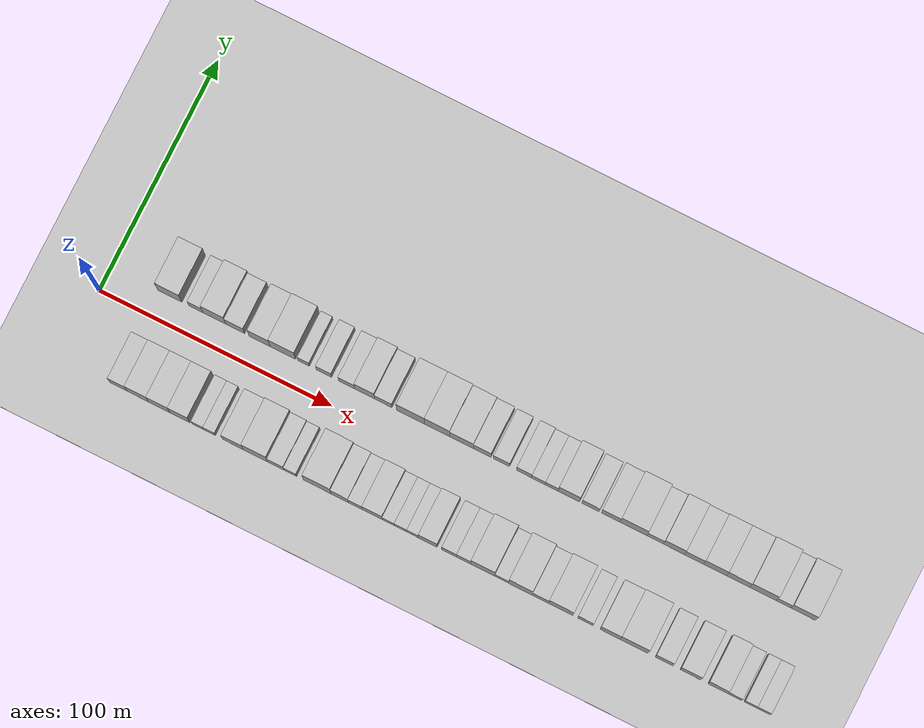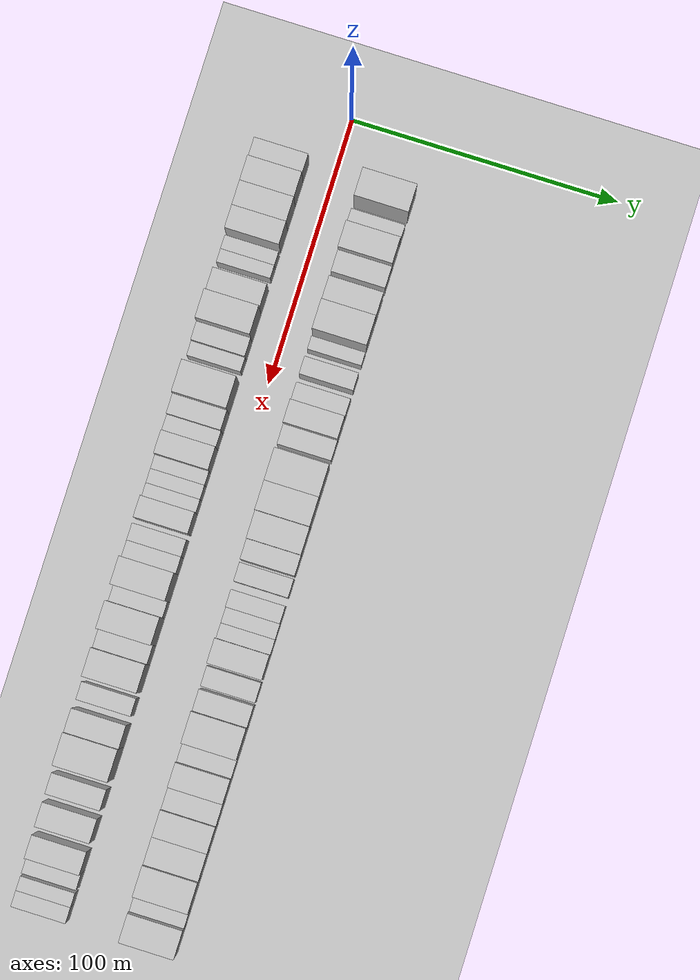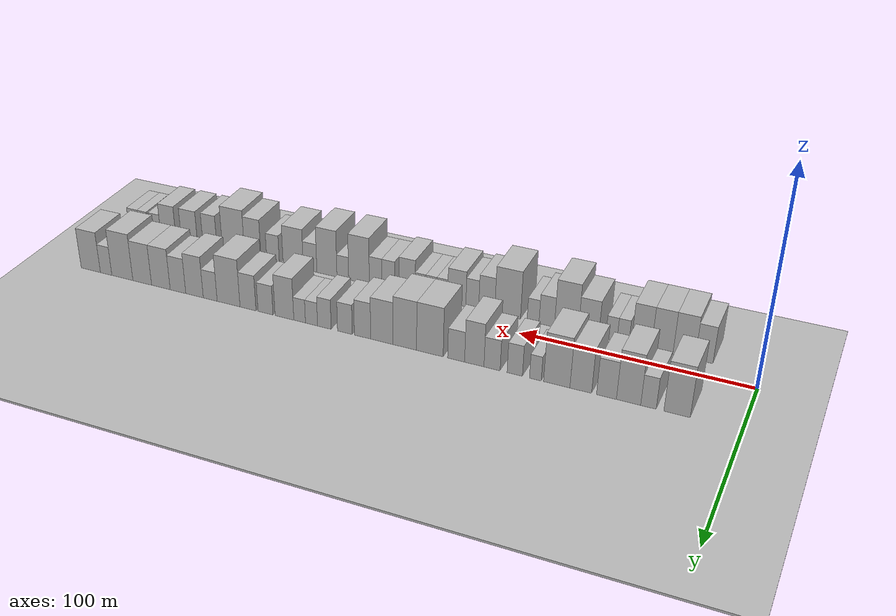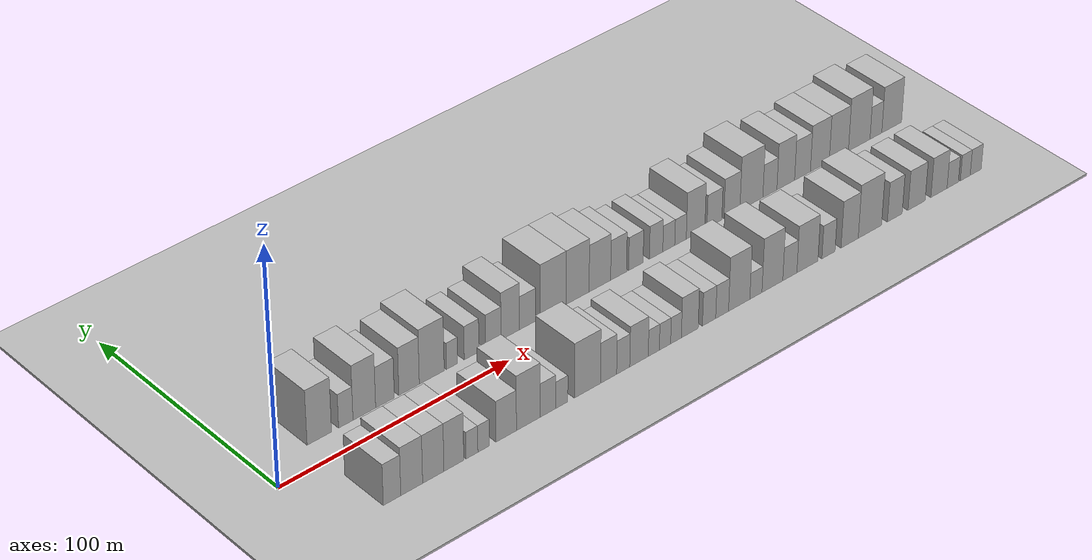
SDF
<?xml version="1.0" encoding="utf-8"?>

<sdf version="1.6">

   <world name="default">

      <gui fullscreen="0">

         <camera name="user_camera">

            <pose>-15 0 4.57585 0 0 0</pose>

            <view_controller>orbit</view_controller>

         </camera>

      </gui>

      <scene>

         <sky>

           <clouds>

             <speed>12</speed>

           </clouds>

         </sky>

         <ambient>0.4 0.4 0.4 1</ambient>

         <background>0.7 0.7 0.7 1</background>

         <shadows>1</shadows>

      </scene>

      <gravity>0 0 -9.8066</gravity>

      <magnetic_field>6e-06 2.3e-05 -4.2e-05</magnetic_field>

      <physics default="0" name="default_physics" type="ode">

         <ode>

            <solver>

               <type>quick</type>

               <iters>10</iters>

               <sor>1.0</sor>

               <use_dynamic_moi_rescaling>0</use_dynamic_moi_rescaling>

            </solver>

            <constraints>

               <cfm>0</cfm>

               <erp>0.2</erp>

               <contact_max_correcting_vel>100</contact_max_correcting_vel>

               <contact_surface_layer>0.001</contact_surface_layer>

            </constraints>

         </ode>

         <max_step_size>0.004</max_step_size>

         <real_time_factor>1</real_time_factor>

         <real_time_update_rate>250</real_time_update_rate>

      </physics>

      <light name="sun" type="directional">

         <cast_shadows>1</cast_shadows>

         <pose>0 0 10 0 0 0</pose>

         <diffuse>0.8 0.8 0.8 1</diffuse>

         <specular>0.2 0.2 0.2 1</specular>

         <attenuation>

            <range>1000</range>

            <constant>0.9</constant>

            <linear>0.01</linear>

            <quadratic>0.001</quadratic>

         </attenuation>

         <direction>-0.5 0.1 -0.9</direction>

      </light>

      <include>

         <name>ground_plane_1</name>

         <uri>model://HANNAS_ground_plane</uri>

         <pose>0 0 0  0 0 0</pose>

      </include>

      <include>

         <name>ground_plane_2</name>

         <uri>model://HANNAS_ground_plane</uri>

         <pose>100 0 0  0 0 0</pose>

      </include>

      <model name="building_1">

         <static>1</static>

         <pose frame="">25.1743 20.0000 0 0.000000 0.000000 1.570796</pose>

         <link name="link">

            <pose frame="">0 0 12.00 0 0 0</pose>

            <collision name="collision">

               <geometry>

                  <box>

                     <size>20.0000 10.3486 24.0000</size>

                  </box>

               </geometry>

               <max_contacts>10</max_contacts>

               <surface>

                  <contact>

                     <ode/>

                  </contact>

                  <bounce/>

                  <friction>

                     <torsional>

                        <ode/>

                     </torsional>

                     <ode/>

                  </friction>

               </surface>

            </collision>

            <visual name="visual">

               <cast_shadows>0</cast_shadows>

               <geometry>

                  <box>

                     <size>20.0000 10.3486 24.0000</size>

                  </box>

               </geometry>

               <material>

                  <script>

                     <uri>model://HANNAS_wall/materials/scripts</uri>

                     <uri>model://HANNAS_wall/materials/textures</uri>

                     <name>vrc/HANNAS_wall</name>

                  </script>

               </material>

            </visual>

            <self_collide>0</self_collide>

            <enable_wind>0</enable_wind>

            <kinematic>0</kinematic>

         </link>

      </model>

      <model name="building_2">

         <static>1</static>

         <pose frame="">36.4311 20.0000 0 0.000000 0.000000 1.570796</pose>

         <link name="link">

            <pose frame="">0 0 7.50 0 0 0</pose>

            <collision name="collision">

               <geometry>

                  <box>

                     <size>20.0000 6.1650 15.0000</size>

                  </box>

               </geometry>

               <max_contacts>10</max_contacts>

               <surface>

                  <contact>

                     <ode/>

                  </contact>

                  <bounce/>

                  <friction>

                     <torsional>

                        <ode/>

                     </torsional>

                     <ode/>

                  </friction>

               </surface>

            </collision>

            <visual name="visual">

               <cast_shadows>0</cast_shadows>

               <geometry>

                  <box>

                     <size>20.0000 6.1650 15.0000</size>

                  </box>

               </geometry>

               <material>

                  <script>

                     <uri>model://HANNAS_wall/materials/scripts</uri>

                     <uri>model://HANNAS_wall/materials/textures</uri>

                     <name>vrc/HANNAS_wall</name>

                  </script>

               </material>

            </visual>

            <self_collide>0</self_collide>

            <enable_wind>0</enable_wind>

            <kinematic>0</kinematic>

         </link>

      </model>

      <model name="building_3">

         <static>1</static>

         <pose frame="">44.3929 20.0000 0 0.000000 0.000000 1.570796</pose>

         <link name="link">

            <pose frame="">0 0 12.00 0 0 0</pose>

            <collision name="collision">

               <geometry>

                  <box>

                     <size>20.0000 9.7587 24.0000</size>

                  </box>

               </geometry>

               <max_contacts>10</max_contacts>

               <surface>

                  <contact>

                     <ode/>

                  </contact>

                  <bounce/>

                  <friction>

                     <torsional>

                        <ode/>

                     </torsional>

                     <ode/>

                  </friction>

               </surface>

            </collision>

            <visual name="visual">

               <cast_shadows>0</cast_shadows>

               <geometry>

                  <box>

                     <size>20.0000 9.7587 24.0000</size>

                  </box>

               </geometry>

               <material>

                  <script>

                     <uri>model://HANNAS_wall/materials/scripts</uri>

                     <uri>model://HANNAS_wall/materials/textures</uri>

                     <name>vrc/HANNAS_wall</name>

                  </script>

               </material>

            </visual>

            <self_collide>0</self_collide>

            <enable_wind>0</enable_wind>

            <kinematic>0</kinematic>

         </link>

      </model>

      <model name="building_4">

         <static>1</static>

         <pose frame="">53.3143 20.0000 0 0.000000 0.000000 1.570796</pose>

         <link name="link">

            <pose frame="">0 0 9.00 0 0 0</pose>

            <collision name="collision">

               <geometry>

                  <box>

                     <size>20.0000 8.0840 18.0000</size>

                  </box>

               </geometry>

               <max_contacts>10</max_contacts>

               <surface>

                  <contact>

                     <ode/>

                  </contact>

                  <bounce/>

                  <friction>

                     <torsional>

                        <ode/>

                     </torsional>

                     <ode/>

                  </friction>

               </surface>

            </collision>

            <visual name="visual">

               <cast_shadows>0</cast_shadows>

               <geometry>

                  <box>

                     <size>20.0000 8.0840 18.0000</size>

                  </box>

               </geometry>

               <material>

                  <script>

                     <uri>model://HANNAS_wall/materials/scripts</uri>

                     <uri>model://HANNAS_wall/materials/textures</uri>

                     <name>vrc/HANNAS_wall</name>

                  </script>

               </material>

            </visual>

            <self_collide>0</self_collide>

            <enable_wind>0</enable_wind>

            <kinematic>0</kinematic>

         </link>

      </model>

      <model name="building_5">

         <static>1</static>

         <pose frame="">63.8279 20.0000 0 0.000000 0.000000 1.570796</pose>

         <link name="link">

            <pose frame="">0 0 10.50 0 0 0</pose>

            <collision name="collision">

               <geometry>

                  <box>

                     <size>20.0000 8.9433 21.0000</size>

                  </box>

               </geometry>

               <max_contacts>10</max_contacts>

               <surface>

                  <contact>

                     <ode/>

                  </contact>

                  <bounce/>

                  <friction>

                     <torsional>

                        <ode/>

                     </torsional>

                     <ode/>

                  </friction>

               </surface>

            </collision>

            <visual name="visual">

               <cast_shadows>0</cast_shadows>

               <geometry>

                  <box>

                     <size>20.0000 8.9433 21.0000</size>

                  </box>

               </geometry>

               <material>

                  <script>

                     <uri>model://HANNAS_wall/materials/scripts</uri>

                     <uri>model://HANNAS_wall/materials/textures</uri>

                     <name>vrc/HANNAS_wall</name>

                  </script>

               </material>

            </visual>

            <self_collide>0</self_collide>

            <enable_wind>0</enable_wind>

            <kinematic>0</kinematic>

         </link>

      </model>

      <model name="building_6">

         <static>1</static>

         <pose frame="">73.7910 20.0000 0 0.000000 0.000000 1.570796</pose>

         <link name="link">

            <pose frame="">0 0 12.00 0 0 0</pose>

            <collision name="collision">

               <geometry>

                  <box>

                     <size>20.0000 10.9828 24.0000</size>

                  </box>

               </geometry>

               <max_contacts>10</max_contacts>

               <surface>

                  <contact>

                     <ode/>

                  </contact>

                  <bounce/>

                  <friction>

                     <torsional>

                        <ode/>

                     </torsional>

                     <ode/>

                  </friction>

               </surface>

            </collision>

            <visual name="visual">

               <cast_shadows>0</cast_shadows>

               <geometry>

                  <box>

                     <size>20.0000 10.9828 24.0000</size>

                  </box>

               </geometry>

               <material>

                  <script>

                     <uri>model://HANNAS_wall/materials/scripts</uri>

                     <uri>model://HANNAS_wall/materials/textures</uri>

                     <name>vrc/HANNAS_wall</name>

                  </script>

               </material>

            </visual>

            <self_collide>0</self_collide>

            <enable_wind>0</enable_wind>

            <kinematic>0</kinematic>

         </link>

      </model>

      <model name="building_7">

         <static>1</static>

         <pose frame="">82.7563 20.0000 0 0.000000 0.000000 1.570796</pose>

         <link name="link">

            <pose frame="">0 0 6.00 0 0 0</pose>

            <collision name="collision">

               <geometry>

                  <box>

                     <size>20.0000 4.9477 12.0000</size>

                  </box>

               </geometry>

               <max_contacts>10</max_contacts>

               <surface>

                  <contact>

                     <ode/>

                  </contact>

                  <bounce/>

                  <friction>

                     <torsional>

                        <ode/>

                     </torsional>

                     <ode/>

                  </friction>

               </surface>

            </collision>

            <visual name="visual">

               <cast_shadows>0</cast_shadows>

               <geometry>

                  <box>

                     <size>20.0000 4.9477 12.0000</size>

                  </box>

               </geometry>

               <material>

                  <script>

                     <uri>model://HANNAS_wall/materials/scripts</uri>

                     <uri>model://HANNAS_wall/materials/textures</uri>

                     <name>vrc/HANNAS_wall</name>

                  </script>

               </material>

            </visual>

            <self_collide>0</self_collide>

            <enable_wind>0</enable_wind>

            <kinematic>0</kinematic>

         </link>

      </model>

      <model name="building_8">

         <static>1</static>

         <pose frame="">91.5076 20.0000 0 0.000000 0.000000 1.570796</pose>

         <link name="link">

            <pose frame="">0 0 7.50 0 0 0</pose>

            <collision name="collision">

               <geometry>

                  <box>

                     <size>20.0000 6.5549 15.0000</size>

                  </box>

               </geometry>

               <max_contacts>10</max_contacts>

               <surface>

                  <contact>

                     <ode/>

                  </contact>

                  <bounce/>

                  <friction>

                     <torsional>

                        <ode/>

                     </torsional>

                     <ode/>

                  </friction>

               </surface>

            </collision>

            <visual name="visual">

               <cast_shadows>0</cast_shadows>

               <geometry>

                  <box>

                     <size>20.0000 6.5549 15.0000</size>

                  </box>

               </geometry>

               <material>

                  <script>

                     <uri>model://HANNAS_wall/materials/scripts</uri>

                     <uri>model://HANNAS_wall/materials/textures</uri>

                     <name>vrc/HANNAS_wall</name>

                  </script>

               </material>

            </visual>

            <self_collide>0</self_collide>

            <enable_wind>0</enable_wind>

            <kinematic>0</kinematic>

         </link>

      </model>

      <model name="building_9">

         <static>1</static>

         <pose frame="">101.2741 20.0000 0 0.000000 0.000000 1.570796</pose>

         <link name="link">

            <pose frame="">0 0 7.50 0 0 0</pose>

            <collision name="collision">

               <geometry>

                  <box>

                     <size>20.0000 6.9781 15.0000</size>

                  </box>

               </geometry>

               <max_contacts>10</max_contacts>

               <surface>

                  <contact>

                     <ode/>

                  </contact>

                  <bounce/>

                  <friction>

                     <torsional>

                        <ode/>

                     </torsional>

                     <ode/>

                  </friction>

               </surface>

            </collision>

            <visual name="visual">

               <cast_shadows>0</cast_shadows>

               <geometry>

                  <box>

                     <size>20.0000 6.9781 15.0000</size>

                  </box>

               </geometry>

               <material>

                  <script>

                     <uri>model://HANNAS_wall/materials/scripts</uri>

                     <uri>model://HANNAS_wall/materials/textures</uri>

                     <name>vrc/HANNAS_wall</name>

                  </script>

               </material>

            </visual>

            <self_collide>0</self_collide>

            <enable_wind>0</enable_wind>

            <kinematic>0</kinematic>

         </link>

      </model>

      <model name="building_10">

         <static>1</static>

         <pose frame="">108.9862 20.0000 0 0.000000 0.000000 1.570796</pose>

         <link name="link">

            <pose frame="">0 0 10.50 0 0 0</pose>

            <collision name="collision">

               <geometry>

                  <box>

                     <size>20.0000 8.4461 21.0000</size>

                  </box>

               </geometry>

               <max_contacts>10</max_contacts>

               <surface>

                  <contact>

                     <ode/>

                  </contact>

                  <bounce/>

                  <friction>

                     <torsional>

                        <ode/>

                     </torsional>

                     <ode/>

                  </friction>

               </surface>

            </collision>

            <visual name="visual">

               <cast_shadows>0</cast_shadows>

               <geometry>

                  <box>

                     <size>20.0000 8.4461 21.0000</size>

                  </box>

               </geometry>

               <material>

                  <script>

                     <uri>model://HANNAS_wall/materials/scripts</uri>

                     <uri>model://HANNAS_wall/materials/textures</uri>

                     <name>vrc/HANNAS_wall</name>

                  </script>

               </material>

            </visual>

            <self_collide>0</self_collide>

            <enable_wind>0</enable_wind>

            <kinematic>0</kinematic>

         </link>

      </model>

      <model name="building_11">

         <static>1</static>

         <pose frame="">116.9474 20.0000 0 0.000000 0.000000 1.570796</pose>

         <link name="link">

            <pose frame="">0 0 7.50 0 0 0</pose>

            <collision name="collision">

               <geometry>

                  <box>

                     <size>20.0000 7.4762 15.0000</size>

                  </box>

               </geometry>

               <max_contacts>10</max_contacts>

               <surface>

                  <contact>

                     <ode/>

                  </contact>

                  <bounce/>

                  <friction>

                     <torsional>

                        <ode/>

                     </torsional>

                     <ode/>

                  </friction>

               </surface>

            </collision>

            <visual name="visual">

               <cast_shadows>0</cast_shadows>

               <geometry>

                  <box>

                     <size>20.0000 7.4762 15.0000</size>

                  </box>

               </geometry>

               <material>

                  <script>

                     <uri>model://HANNAS_wall/materials/scripts</uri>

                     <uri>model://HANNAS_wall/materials/textures</uri>

                     <name>vrc/HANNAS_wall</name>

                  </script>

               </material>

            </visual>

            <self_collide>0</self_collide>

            <enable_wind>0</enable_wind>

            <kinematic>0</kinematic>

         </link>

      </model>

      <model name="building_12">

         <static>1</static>

         <pose frame="">128.6530 20.0000 0 0.000000 0.000000 1.570796</pose>

         <link name="link">

            <pose frame="">0 0 12.00 0 0 0</pose>

            <collision name="collision">

               <geometry>

                  <box>

                     <size>20.0000 11.9351 24.0000</size>

                  </box>

               </geometry>

               <max_contacts>10</max_contacts>

               <surface>

                  <contact>

                     <ode/>

                  </contact>

                  <bounce/>

                  <friction>

                     <torsional>

                        <ode/>

                     </torsional>

                     <ode/>

                  </friction>

               </surface>

            </collision>

            <visual name="visual">

               <cast_shadows>0</cast_shadows>

               <geometry>

                  <box>

                     <size>20.0000 11.9351 24.0000</size>

                  </box>

               </geometry>

               <material>

                  <script>

                     <uri>model://HANNAS_wall/materials/scripts</uri>

                     <uri>model://HANNAS_wall/materials/textures</uri>

                     <name>vrc/HANNAS_wall</name>

                  </script>

               </material>

            </visual>

            <self_collide>0</self_collide>

            <enable_wind>0</enable_wind>

            <kinematic>0</kinematic>

         </link>

      </model>

      <model name="building_13">

         <static>1</static>

         <pose frame="">140.0037 20.0000 0 0.000000 0.000000 1.570796</pose>

         <link name="link">

            <pose frame="">0 0 12.00 0 0 0</pose>

            <collision name="collision">

               <geometry>

                  <box>

                     <size>20.0000 10.7661 24.0000</size>

                  </box>

               </geometry>

               <max_contacts>10</max_contacts>

               <surface>

                  <contact>

                     <ode/>

                  </contact>

                  <bounce/>

                  <friction>

                     <torsional>

                        <ode/>

                     </torsional>

                     <ode/>

                  </friction>

               </surface>

            </collision>

            <visual name="visual">

               <cast_shadows>0</cast_shadows>

               <geometry>

                  <box>

                     <size>20.0000 10.7661 24.0000</size>

                  </box>

               </geometry>

               <material>

                  <script>

                     <uri>model://HANNAS_wall/materials/scripts</uri>

                     <uri>model://HANNAS_wall/materials/textures</uri>

                     <name>vrc/HANNAS_wall</name>

                  </script>

               </material>

            </visual>

            <self_collide>0</self_collide>

            <enable_wind>0</enable_wind>

            <kinematic>0</kinematic>

         </link>

      </model>

      <model name="building_14">

         <static>1</static>

         <pose frame="">150.4808 20.0000 0 0.000000 0.000000 1.570796</pose>

         <link name="link">

            <pose frame="">0 0 10.50 0 0 0</pose>

            <collision name="collision">

               <geometry>

                  <box>

                     <size>20.0000 10.1882 21.0000</size>

                  </box>

               </geometry>

               <max_contacts>10</max_contacts>

               <surface>

                  <contact>

                     <ode/>

                  </contact>

                  <bounce/>

                  <friction>

                     <torsional>

                        <ode/>

                     </torsional>

                     <ode/>

                  </friction>

               </surface>

            </collision>

            <visual name="visual">

               <cast_shadows>0</cast_shadows>

               <geometry>

                  <box>

                     <size>20.0000 10.1882 21.0000</size>

                  </box>

               </geometry>

               <material>

                  <script>

                     <uri>model://HANNAS_wall/materials/scripts</uri>

                     <uri>model://HANNAS_wall/materials/textures</uri>

                     <name>vrc/HANNAS_wall</name>

                  </script>

               </material>

            </visual>

            <self_collide>0</self_collide>

            <enable_wind>0</enable_wind>

            <kinematic>0</kinematic>

         </link>

      </model>

      <model name="building_15">

         <static>1</static>

         <pose frame="">159.3517 20.0000 0 0.000000 0.000000 1.570796</pose>

         <link name="link">

            <pose frame="">0 0 9.00 0 0 0</pose>

            <collision name="collision">

               <geometry>

                  <box>

                     <size>20.0000 7.5536 18.0000</size>

                  </box>

               </geometry>

               <max_contacts>10</max_contacts>

               <surface>

                  <contact>

                     <ode/>

                  </contact>

                  <bounce/>

                  <friction>

                     <torsional>

                        <ode/>

                     </torsional>

                     <ode/>

                  </friction>

               </surface>

            </collision>

            <visual name="visual">

               <cast_shadows>0</cast_shadows>

               <geometry>

                  <box>

                     <size>20.0000 7.5536 18.0000</size>

                  </box>

               </geometry>

               <material>

                  <script>

                     <uri>model://HANNAS_wall/materials/scripts</uri>

                     <uri>model://HANNAS_wall/materials/textures</uri>

                     <name>vrc/HANNAS_wall</name>

                  </script>

               </material>

            </visual>

            <self_collide>0</self_collide>

            <enable_wind>0</enable_wind>

            <kinematic>0</kinematic>

         </link>

      </model>

      <model name="building_16">

         <static>1</static>

         <pose frame="">167.5825 20.0000 0 0.000000 0.000000 1.570796</pose>

         <link name="link">

            <pose frame="">0 0 7.50 0 0 0</pose>

            <collision name="collision">

               <geometry>

                  <box>

                     <size>20.0000 6.9079 15.0000</size>

                  </box>

               </geometry>

               <max_contacts>10</max_contacts>

               <surface>

                  <contact>

                     <ode/>

                  </contact>

                  <bounce/>

                  <friction>

                     <torsional>

                        <ode/>

                     </torsional>

                     <ode/>

                  </friction>

               </surface>

            </collision>

            <visual name="visual">

               <cast_shadows>0</cast_shadows>

               <geometry>

                  <box>

                     <size>20.0000 6.9079 15.0000</size>

                  </box>

               </geometry>

               <material>

                  <script>

                     <uri>model://HANNAS_wall/materials/scripts</uri>

                     <uri>model://HANNAS_wall/materials/textures</uri>

                     <name>vrc/HANNAS_wall</name>

                  </script>

               </material>

            </visual>

            <self_collide>0</self_collide>

            <enable_wind>0</enable_wind>

            <kinematic>0</kinematic>

         </link>

      </model>

      <model name="building_17">

         <static>1</static>

         <pose frame="">177.2707 20.0000 0 0.000000 0.000000 1.570796</pose>

         <link name="link">

            <pose frame="">0 0 7.50 0 0 0</pose>

            <collision name="collision">

               <geometry>

                  <box>

                     <size>20.0000 6.4686 15.0000</size>

                  </box>

               </geometry>

               <max_contacts>10</max_contacts>

               <surface>

                  <contact>

                     <ode/>

                  </contact>

                  <bounce/>

                  <friction>

                     <torsional>

                        <ode/>

                     </torsional>

                     <ode/>

                  </friction>

               </surface>

            </collision>

            <visual name="visual">

               <cast_shadows>0</cast_shadows>

               <geometry>

                  <box>

                     <size>20.0000 6.4686 15.0000</size>

                  </box>

               </geometry>

               <material>

                  <script>

                     <uri>model://HANNAS_wall/materials/scripts</uri>

                     <uri>model://HANNAS_wall/materials/textures</uri>

                     <name>vrc/HANNAS_wall</name>

                  </script>

               </material>

            </visual>

            <self_collide>0</self_collide>

            <enable_wind>0</enable_wind>

            <kinematic>0</kinematic>

         </link>

      </model>

      <model name="building_18">

         <static>1</static>

         <pose frame="">183.3950 20.0000 0 0.000000 0.000000 1.570796</pose>

         <link name="link">

            <pose frame="">0 0 6.00 0 0 0</pose>

            <collision name="collision">

               <geometry>

                  <box>

                     <size>20.0000 5.7799 12.0000</size>

                  </box>

               </geometry>

               <max_contacts>10</max_contacts>

               <surface>

                  <contact>

                     <ode/>

                  </contact>

                  <bounce/>

                  <friction>

                     <torsional>

                        <ode/>

                     </torsional>

                     <ode/>

                  </friction>

               </surface>

            </collision>

            <visual name="visual">

               <cast_shadows>0</cast_shadows>

               <geometry>

                  <box>

                     <size>20.0000 5.7799 12.0000</size>

                  </box>

               </geometry>

               <material>

                  <script>

                     <uri>model://HANNAS_wall/materials/scripts</uri>

                     <uri>model://HANNAS_wall/materials/textures</uri>

                     <name>vrc/HANNAS_wall</name>

                  </script>

               </material>

            </visual>

            <self_collide>0</self_collide>

            <enable_wind>0</enable_wind>

            <kinematic>0</kinematic>

         </link>

      </model>

      <model name="building_19">

         <static>1</static>

         <pose frame="">189.0943 20.0000 0 0.000000 0.000000 1.570796</pose>

         <link name="link">

            <pose frame="">0 0 6.00 0 0 0</pose>

            <collision name="collision">

               <geometry>

                  <box>

                     <size>20.0000 5.6186 12.0000</size>

                  </box>

               </geometry>

               <max_contacts>10</max_contacts>

               <surface>

                  <contact>

                     <ode/>

                  </contact>

                  <bounce/>

                  <friction>

                     <torsional>

                        <ode/>

                     </torsional>

                     <ode/>

                  </friction>

               </surface>

            </collision>

            <visual name="visual">

               <cast_shadows>0</cast_shadows>

               <geometry>

                  <box>

                     <size>20.0000 5.6186 12.0000</size>

                  </box>

               </geometry>

               <material>

                  <script>

                     <uri>model://HANNAS_wall/materials/scripts</uri>

                     <uri>model://HANNAS_wall/materials/textures</uri>

                     <name>vrc/HANNAS_wall</name>

                  </script>

               </material>

            </visual>

            <self_collide>0</self_collide>

            <enable_wind>0</enable_wind>

            <kinematic>0</kinematic>

         </link>

      </model>

      <model name="building_20">

         <static>1</static>

         <pose frame="">196.4568 20.0000 0 0.000000 0.000000 1.570796</pose>

         <link name="link">

            <pose frame="">0 0 10.50 0 0 0</pose>

            <collision name="collision">

               <geometry>

                  <box>

                     <size>20.0000 9.1064 21.0000</size>

                  </box>

               </geometry>

               <max_contacts>10</max_contacts>

               <surface>

                  <contact>

                     <ode/>

                  </contact>

                  <bounce/>

                  <friction>

                     <torsional>

                        <ode/>

                     </torsional>

                     <ode/>

                  </friction>

               </surface>

            </collision>

            <visual name="visual">

               <cast_shadows>0</cast_shadows>

               <geometry>

                  <box>

                     <size>20.0000 9.1064 21.0000</size>

                  </box>

               </geometry>

               <material>

                  <script>

                     <uri>model://HANNAS_wall/materials/scripts</uri>

                     <uri>model://HANNAS_wall/materials/textures</uri>

                     <name>vrc/HANNAS_wall</name>

                  </script>

               </material>

            </visual>

            <self_collide>0</self_collide>

            <enable_wind>0</enable_wind>

            <kinematic>0</kinematic>

         </link>

      </model>

      <model name="building_21">

         <static>1</static>

         <pose frame="">205.6978 20.0000 0 0.000000 0.000000 1.570796</pose>

         <link name="link">

            <pose frame="">0 0 7.50 0 0 0</pose>

            <collision name="collision">

               <geometry>

                  <box>

                     <size>20.0000 7.3757 15.0000</size>

                  </box>

               </geometry>

               <max_contacts>10</max_contacts>

               <surface>

                  <contact>

                     <ode/>

                  </contact>

                  <bounce/>

                  <friction>

                     <torsional>

                        <ode/>

                     </torsional>

                     <ode/>

                  </friction>

               </surface>

            </collision>

            <visual name="visual">

               <cast_shadows>0</cast_shadows>

               <geometry>

                  <box>

                     <size>20.0000 7.3757 15.0000</size>

                  </box>

               </geometry>

               <material>

                  <script>

                     <uri>model://HANNAS_wall/materials/scripts</uri>

                     <uri>model://HANNAS_wall/materials/textures</uri>

                     <name>vrc/HANNAS_wall</name>

                  </script>

               </material>

            </visual>

            <self_collide>0</self_collide>

            <enable_wind>0</enable_wind>

            <kinematic>0</kinematic>

         </link>

      </model>

      <model name="building_22">

         <static>1</static>

         <pose frame="">214.3622 20.0000 0 0.000000 0.000000 1.570796</pose>

         <link name="link">

            <pose frame="">0 0 9.00 0 0 0</pose>

            <collision name="collision">

               <geometry>

                  <box>

                     <size>20.0000 7.9530 18.0000</size>

                  </box>

               </geometry>

               <max_contacts>10</max_contacts>

               <surface>

                  <contact>

                     <ode/>

                  </contact>

                  <bounce/>

                  <friction>

                     <torsional>

                        <ode/>

                     </torsional>

                     <ode/>

                  </friction>

               </surface>

            </collision>

            <visual name="visual">

               <cast_shadows>0</cast_shadows>

               <geometry>

                  <box>

                     <size>20.0000 7.9530 18.0000</size>

                  </box>

               </geometry>

               <material>

                  <script>

                     <uri>model://HANNAS_wall/materials/scripts</uri>

                     <uri>model://HANNAS_wall/materials/textures</uri>

                     <name>vrc/HANNAS_wall</name>

                  </script>

               </material>

            </visual>

            <self_collide>0</self_collide>

            <enable_wind>0</enable_wind>

            <kinematic>0</kinematic>

         </link>

      </model>

      <model name="building_23">

         <static>1</static>

         <pose frame="">224.0813 20.0000 0 0.000000 0.000000 1.570796</pose>

         <link name="link">

            <pose frame="">0 0 12.00 0 0 0</pose>

            <collision name="collision">

               <geometry>

                  <box>

                     <size>20.0000 11.4852 24.0000</size>

                  </box>

               </geometry>

               <max_contacts>10</max_contacts>

               <surface>

                  <contact>

                     <ode/>

                  </contact>

                  <bounce/>

                  <friction>

                     <torsional>

                        <ode/>

                     </torsional>

                     <ode/>

                  </friction>

               </surface>

            </collision>

            <visual name="visual">

               <cast_shadows>0</cast_shadows>

               <geometry>

                  <box>

                     <size>20.0000 11.4852 24.0000</size>

                  </box>

               </geometry>

               <material>

                  <script>

                     <uri>model://HANNAS_wall/materials/scripts</uri>

                     <uri>model://HANNAS_wall/materials/textures</uri>

                     <name>vrc/HANNAS_wall</name>

                  </script>

               </material>

            </visual>

            <self_collide>0</self_collide>

            <enable_wind>0</enable_wind>

            <kinematic>0</kinematic>

         </link>

      </model>

      <model name="building_24">

         <static>1</static>

         <pose frame="">233.3610 20.0000 0 0.000000 0.000000 1.570796</pose>

         <link name="link">

            <pose frame="">0 0 7.50 0 0 0</pose>

            <collision name="collision">

               <geometry>

                  <box>

                     <size>20.0000 7.0742 15.0000</size>

                  </box>

               </geometry>

               <max_contacts>10</max_contacts>

               <surface>

                  <contact>

                     <ode/>

                  </contact>

                  <bounce/>

                  <friction>

                     <torsional>

                        <ode/>

                     </torsional>

                     <ode/>

                  </friction>

               </surface>

            </collision>

            <visual name="visual">

               <cast_shadows>0</cast_shadows>

               <geometry>

                  <box>

                     <size>20.0000 7.0742 15.0000</size>

                  </box>

               </geometry>

               <material>

                  <script>

                     <uri>model://HANNAS_wall/materials/scripts</uri>

                     <uri>model://HANNAS_wall/materials/textures</uri>

                     <name>vrc/HANNAS_wall</name>

                  </script>

               </material>

            </visual>

            <self_collide>0</self_collide>

            <enable_wind>0</enable_wind>

            <kinematic>0</kinematic>

         </link>

      </model>

      <model name="building_25">

         <static>1</static>

         <pose frame="">241.3886 20.0000 0 0.000000 0.000000 1.570796</pose>

         <link name="link">

            <pose frame="">0 0 10.50 0 0 0</pose>

            <collision name="collision">

               <geometry>

                  <box>

                     <size>20.0000 8.9811 21.0000</size>

                  </box>

               </geometry>

               <max_contacts>10</max_contacts>

               <surface>

                  <contact>

                     <ode/>

                  </contact>

                  <bounce/>

                  <friction>

                     <torsional>

                        <ode/>

                     </torsional>

                     <ode/>

                  </friction>

               </surface>

            </collision>

            <visual name="visual">

               <cast_shadows>0</cast_shadows>

               <geometry>

                  <box>

                     <size>20.0000 8.9811 21.0000</size>

                  </box>

               </geometry>

               <material>

                  <script>

                     <uri>model://HANNAS_wall/materials/scripts</uri>

                     <uri>model://HANNAS_wall/materials/textures</uri>

                     <name>vrc/HANNAS_wall</name>

                  </script>

               </material>

            </visual>

            <self_collide>0</self_collide>

            <enable_wind>0</enable_wind>

            <kinematic>0</kinematic>

         </link>

      </model>

      <model name="building_26">

         <static>1</static>

         <pose frame="">249.9192 20.0000 0 0.000000 0.000000 1.570796</pose>

         <link name="link">

            <pose frame="">0 0 9.00 0 0 0</pose>

            <collision name="collision">

               <geometry>

                  <box>

                     <size>20.0000 8.0800 18.0000</size>

                  </box>

               </geometry>

               <max_contacts>10</max_contacts>

               <surface>

                  <contact>

                     <ode/>

                  </contact>

                  <bounce/>

                  <friction>

                     <torsional>

                        <ode/>

                     </torsional>

                     <ode/>

                  </friction>

               </surface>

            </collision>

            <visual name="visual">

               <cast_shadows>0</cast_shadows>

               <geometry>

                  <box>

                     <size>20.0000 8.0800 18.0000</size>

                  </box>

               </geometry>

               <material>

                  <script>

                     <uri>model://HANNAS_wall/materials/scripts</uri>

                     <uri>model://HANNAS_wall/materials/textures</uri>

                     <name>vrc/HANNAS_wall</name>

                  </script>

               </material>

            </visual>

            <self_collide>0</self_collide>

            <enable_wind>0</enable_wind>

            <kinematic>0</kinematic>

         </link>

      </model>

      <model name="building_27">

         <static>1</static>

         <pose frame="">258.8169 20.0000 0 0.000000 0.000000 1.570796</pose>

         <link name="link">

            <pose frame="">0 0 10.50 0 0 0</pose>

            <collision name="collision">

               <geometry>

                  <box>

                     <size>20.0000 9.7153 21.0000</size>

                  </box>

               </geometry>

               <max_contacts>10</max_contacts>

               <surface>

                  <contact>

                     <ode/>

                  </contact>

                  <bounce/>

                  <friction>

                     <torsional>

                        <ode/>

                     </torsional>

                     <ode/>

                  </friction>

               </surface>

            </collision>

            <visual name="visual">

               <cast_shadows>0</cast_shadows>

               <geometry>

                  <box>

                     <size>20.0000 9.7153 21.0000</size>

                  </box>

               </geometry>

               <material>

                  <script>

                     <uri>model://HANNAS_wall/materials/scripts</uri>

                     <uri>model://HANNAS_wall/materials/textures</uri>

                     <name>vrc/HANNAS_wall</name>

                  </script>

               </material>

            </visual>

            <self_collide>0</self_collide>

            <enable_wind>0</enable_wind>

            <kinematic>0</kinematic>

         </link>

      </model>

      <model name="building_28">

         <static>1</static>

         <pose frame="">268.6389 20.0000 0 0.000000 0.000000 1.570796</pose>

         <link name="link">

            <pose frame="">0 0 10.50 0 0 0</pose>

            <collision name="collision">

               <geometry>

                  <box>

                     <size>20.0000 9.9288 21.0000</size>

                  </box>

               </geometry>

               <max_contacts>10</max_contacts>

               <surface>

                  <contact>

                     <ode/>

                  </contact>

                  <bounce/>

                  <friction>

                     <torsional>

                        <ode/>

                     </torsional>

                     <ode/>

                  </friction>

               </surface>

            </collision>

            <visual name="visual">

               <cast_shadows>0</cast_shadows>

               <geometry>

                  <box>

                     <size>20.0000 9.9288 21.0000</size>

                  </box>

               </geometry>

               <material>

                  <script>

                     <uri>model://HANNAS_wall/materials/scripts</uri>

                     <uri>model://HANNAS_wall/materials/textures</uri>

                     <name>vrc/HANNAS_wall</name>

                  </script>

               </material>

            </visual>

            <self_collide>0</self_collide>

            <enable_wind>0</enable_wind>

            <kinematic>0</kinematic>

         </link>

      </model>

      <model name="building_29">

         <static>1</static>

         <pose frame="">279.2362 20.0000 0 0.000000 0.000000 1.570796</pose>

         <link name="link">

            <pose frame="">0 0 12.00 0 0 0</pose>

            <collision name="collision">

               <geometry>

                  <box>

                     <size>20.0000 11.2658 24.0000</size>

                  </box>

               </geometry>

               <max_contacts>10</max_contacts>

               <surface>

                  <contact>

                     <ode/>

                  </contact>

                  <bounce/>

                  <friction>

                     <torsional>

                        <ode/>

                     </torsional>

                     <ode/>

                  </friction>

               </surface>

            </collision>

            <visual name="visual">

               <cast_shadows>0</cast_shadows>

               <geometry>

                  <box>

                     <size>20.0000 11.2658 24.0000</size>

                  </box>

               </geometry>

               <material>

                  <script>

                     <uri>model://HANNAS_wall/materials/scripts</uri>

                     <uri>model://HANNAS_wall/materials/textures</uri>

                     <name>vrc/HANNAS_wall</name>

                  </script>

               </material>

            </visual>

            <self_collide>0</self_collide>

            <enable_wind>0</enable_wind>

            <kinematic>0</kinematic>

         </link>

      </model>

      <model name="building_30">

         <static>1</static>

         <pose frame="">287.9729 20.0000 0 0.000000 0.000000 1.570796</pose>

         <link name="link">

            <pose frame="">0 0 7.50 0 0 0</pose>

            <collision name="collision">

               <geometry>

                  <box>

                     <size>20.0000 6.2075 15.0000</size>

                  </box>

               </geometry>

               <max_contacts>10</max_contacts>

               <surface>

                  <contact>

                     <ode/>

                  </contact>

                  <bounce/>

                  <friction>

                     <torsional>

                        <ode/>

                     </torsional>

                     <ode/>

                  </friction>

               </surface>

            </collision>

            <visual name="visual">

               <cast_shadows>0</cast_shadows>

               <geometry>

                  <box>

                     <size>20.0000 6.2075 15.0000</size>

                  </box>

               </geometry>

               <material>

                  <script>

                     <uri>model://HANNAS_wall/materials/scripts</uri>

                     <uri>model://HANNAS_wall/materials/textures</uri>

                     <name>vrc/HANNAS_wall</name>

                  </script>

               </material>

            </visual>

            <self_collide>0</self_collide>

            <enable_wind>0</enable_wind>

            <kinematic>0</kinematic>

         </link>

      </model>

      <model name="building_31">

         <static>1</static>

         <pose frame="">296.3092 20.0000 0 0.000000 0.000000 1.570796</pose>

         <link name="link">

            <pose frame="">0 0 10.50 0 0 0</pose>

            <collision name="collision">

               <geometry>

                  <box>

                     <size>20.0000 10.4650 21.0000</size>

                  </box>

               </geometry>

               <max_contacts>10</max_contacts>

               <surface>

                  <contact>

                     <ode/>

                  </contact>

                  <bounce/>

                  <friction>

                     <torsional>

                        <ode/>

                     </torsional>

                     <ode/>

                  </friction>

               </surface>

            </collision>

            <visual name="visual">

               <cast_shadows>0</cast_shadows>

               <geometry>

                  <box>

                     <size>20.0000 10.4650 21.0000</size>

                  </box>

               </geometry>

               <material>

                  <script>

                     <uri>model://HANNAS_wall/materials/scripts</uri>

                     <uri>model://HANNAS_wall/materials/textures</uri>

                     <name>vrc/HANNAS_wall</name>

                  </script>

               </material>

            </visual>

            <self_collide>0</self_collide>

            <enable_wind>0</enable_wind>

            <kinematic>0</kinematic>

         </link>

      </model>

      <model name="building_32">

         <static>1</static>

         <pose frame="">23.6801 -20.0000 0 0.000000 0.000000 1.570796</pose>

         <link name="link">

            <pose frame="">0 0 9.00 0 0 0</pose>

            <collision name="collision">

               <geometry>

                  <box>

                     <size>20.0000 7.3602 18.0000</size>

                  </box>

               </geometry>

               <max_contacts>10</max_contacts>

               <surface>

                  <contact>

                     <ode/>

                  </contact>

                  <bounce/>

                  <friction>

                     <torsional>

                        <ode/>

                     </torsional>

                     <ode/>

                  </friction>

               </surface>

            </collision>

            <visual name="visual">

               <cast_shadows>0</cast_shadows>

               <geometry>

                  <box>

                     <size>20.0000 7.3602 18.0000</size>

                  </box>

               </geometry>

               <material>

                  <script>

                     <uri>model://HANNAS_wall/materials/scripts</uri>

                     <uri>model://HANNAS_wall/materials/textures</uri>

                     <name>vrc/HANNAS_wall</name>

                  </script>

               </material>

            </visual>

            <self_collide>0</self_collide>

            <enable_wind>0</enable_wind>

            <kinematic>0</kinematic>

         </link>

      </model>

      <model name="building_33">

         <static>1</static>

         <pose frame="">31.9837 -20.0000 0 0.000000 0.000000 1.570796</pose>

         <link name="link">

            <pose frame="">0 0 10.50 0 0 0</pose>

            <collision name="collision">

               <geometry>

                  <box>

                     <size>20.0000 9.2469 21.0000</size>

                  </box>

               </geometry>

               <max_contacts>10</max_contacts>

               <surface>

                  <contact>

                     <ode/>

                  </contact>

                  <bounce/>

                  <friction>

                     <torsional>

                        <ode/>

                     </torsional>

                     <ode/>

                  </friction>

               </surface>

            </collision>

            <visual name="visual">

               <cast_shadows>0</cast_shadows>

               <geometry>

                  <box>

                     <size>20.0000 9.2469 21.0000</size>

                  </box>

               </geometry>

               <material>

                  <script>

                     <uri>model://HANNAS_wall/materials/scripts</uri>

                     <uri>model://HANNAS_wall/materials/textures</uri>

                     <name>vrc/HANNAS_wall</name>

                  </script>

               </material>

            </visual>

            <self_collide>0</self_collide>

            <enable_wind>0</enable_wind>

            <kinematic>0</kinematic>

         </link>

      </model>

      <model name="building_34">

         <static>1</static>

         <pose frame="">41.1526 -20.0000 0 0.000000 0.000000 1.570796</pose>

         <link name="link">

            <pose frame="">0 0 10.50 0 0 0</pose>

            <collision name="collision">

               <geometry>

                  <box>

                     <size>20.0000 9.0909 21.0000</size>

                  </box>

               </geometry>

               <max_contacts>10</max_contacts>

               <surface>

                  <contact>

                     <ode/>

                  </contact>

                  <bounce/>

                  <friction>

                     <torsional>

                        <ode/>

                     </torsional>

                     <ode/>

                  </friction>

               </surface>

            </collision>

            <visual name="visual">

               <cast_shadows>0</cast_shadows>

               <geometry>

                  <box>

                     <size>20.0000 9.0909 21.0000</size>

                  </box>

               </geometry>

               <material>

                  <script>

                     <uri>model://HANNAS_wall/materials/scripts</uri>

                     <uri>model://HANNAS_wall/materials/textures</uri>

                     <name>vrc/HANNAS_wall</name>

                  </script>

               </material>

            </visual>

            <self_collide>0</self_collide>

            <enable_wind>0</enable_wind>

            <kinematic>0</kinematic>

         </link>

      </model>

      <model name="building_35">

         <static>1</static>

         <pose frame="">49.9651 -20.0000 0 0.000000 0.000000 1.570796</pose>

         <link name="link">

            <pose frame="">0 0 10.50 0 0 0</pose>

            <collision name="collision">

               <geometry>

                  <box>

                     <size>20.0000 8.5342 21.0000</size>

                  </box>

               </geometry>

               <max_contacts>10</max_contacts>

               <surface>

                  <contact>

                     <ode/>

                  </contact>

                  <bounce/>

                  <friction>

                     <torsional>

                        <ode/>

                     </torsional>

                     <ode/>

                  </friction>

               </surface>

            </collision>

            <visual name="visual">

               <cast_shadows>0</cast_shadows>

               <geometry>

                  <box>

                     <size>20.0000 8.5342 21.0000</size>

                  </box>

               </geometry>

               <material>

                  <script>

                     <uri>model://HANNAS_wall/materials/scripts</uri>

                     <uri>model://HANNAS_wall/materials/textures</uri>

                     <name>vrc/HANNAS_wall</name>

                  </script>

               </material>

            </visual>

            <self_collide>0</self_collide>

            <enable_wind>0</enable_wind>

            <kinematic>0</kinematic>

         </link>

      </model>

      <model name="building_36">

         <static>1</static>

         <pose frame="">57.7911 -20.0000 0 0.000000 0.000000 1.570796</pose>

         <link name="link">

            <pose frame="">0 0 6.00 0 0 0</pose>

            <collision name="collision">

               <geometry>

                  <box>

                     <size>20.0000 5.1178 12.0000</size>

                  </box>

               </geometry>

               <max_contacts>10</max_contacts>

               <surface>

                  <contact>

                     <ode/>

                  </contact>

                  <bounce/>

                  <friction>

                     <torsional>

                        <ode/>

                     </torsional>

                     <ode/>

                  </friction>

               </surface>

            </collision>

            <visual name="visual">

               <cast_shadows>0</cast_shadows>

               <geometry>

                  <box>

                     <size>20.0000 5.1178 12.0000</size>

                  </box>

               </geometry>

               <material>

                  <script>

                     <uri>model://HANNAS_wall/materials/scripts</uri>

                     <uri>model://HANNAS_wall/materials/textures</uri>

                     <name>vrc/HANNAS_wall</name>

                  </script>

               </material>

            </visual>

            <self_collide>0</self_collide>

            <enable_wind>0</enable_wind>

            <kinematic>0</kinematic>

         </link>

      </model>

      <model name="building_37">

         <static>1</static>

         <pose frame="">62.8131 -20.0000 0 0.000000 0.000000 1.570796</pose>

         <link name="link">

            <pose frame="">0 0 6.00 0 0 0</pose>

            <collision name="collision">

               <geometry>

                  <box>

                     <size>20.0000 4.9261 12.0000</size>

                  </box>

               </geometry>

               <max_contacts>10</max_contacts>

               <surface>

                  <contact>

                     <ode/>

                  </contact>

                  <bounce/>

                  <friction>

                     <torsional>

                        <ode/>

                     </torsional>

                     <ode/>

                  </friction>

               </surface>

            </collision>

            <visual name="visual">

               <cast_shadows>0</cast_shadows>

               <geometry>

                  <box>

                     <size>20.0000 4.9261 12.0000</size>

                  </box>

               </geometry>

               <material>

                  <script>

                     <uri>model://HANNAS_wall/materials/scripts</uri>

                     <uri>model://HANNAS_wall/materials/textures</uri>

                     <name>vrc/HANNAS_wall</name>

                  </script>

               </material>

            </visual>

            <self_collide>0</self_collide>

            <enable_wind>0</enable_wind>

            <kinematic>0</kinematic>

         </link>

      </model>

      <model name="building_38">

         <static>1</static>

         <pose frame="">72.7367 -20.0000 0 0.000000 0.000000 1.570796</pose>

         <link name="link">

            <pose frame="">0 0 9.00 0 0 0</pose>

            <collision name="collision">

               <geometry>

                  <box>

                     <size>20.0000 8.9212 18.0000</size>

                  </box>

               </geometry>

               <max_contacts>10</max_contacts>

               <surface>

                  <contact>

                     <ode/>

                  </contact>

                  <bounce/>

                  <friction>

                     <torsional>

                        <ode/>

                     </torsional>

                     <ode/>

                  </friction>

               </surface>

            </collision>

            <visual name="visual">

               <cast_shadows>0</cast_shadows>

               <geometry>

                  <box>

                     <size>20.0000 8.9212 18.0000</size>

                  </box>

               </geometry>

               <material>

                  <script>

                     <uri>model://HANNAS_wall/materials/scripts</uri>

                     <uri>model://HANNAS_wall/materials/textures</uri>

                     <name>vrc/HANNAS_wall</name>

                  </script>

               </material>

            </visual>

            <self_collide>0</self_collide>

            <enable_wind>0</enable_wind>

            <kinematic>0</kinematic>

         </link>

      </model>

      <model name="building_39">

         <static>1</static>

         <pose frame="">82.4959 -20.0000 0 0.000000 0.000000 1.570796</pose>

         <link name="link">

            <pose frame="">0 0 12.00 0 0 0</pose>

            <collision name="collision">

               <geometry>

                  <box>

                     <size>20.0000 10.5970 24.0000</size>

                  </box>

               </geometry>

               <max_contacts>10</max_contacts>

               <surface>

                  <contact>

                     <ode/>

                  </contact>

                  <bounce/>

                  <friction>

                     <torsional>

                        <ode/>

                     </torsional>

                     <ode/>

                  </friction>

               </surface>

            </collision>

            <visual name="visual">

               <cast_shadows>0</cast_shadows>

               <geometry>

                  <box>

                     <size>20.0000 10.5970 24.0000</size>

                  </box>

               </geometry>

               <material>

                  <script>

                     <uri>model://HANNAS_wall/materials/scripts</uri>

                     <uri>model://HANNAS_wall/materials/textures</uri>

                     <name>vrc/HANNAS_wall</name>

                  </script>

               </material>

            </visual>

            <self_collide>0</self_collide>

            <enable_wind>0</enable_wind>

            <kinematic>0</kinematic>

         </link>

      </model>

      <model name="building_40">

         <static>1</static>

         <pose frame="">91.2389 -20.0000 0 0.000000 0.000000 1.570796</pose>

         <link name="link">

            <pose frame="">0 0 7.50 0 0 0</pose>

            <collision name="collision">

               <geometry>

                  <box>

                     <size>20.0000 6.8890 15.0000</size>

                  </box>

               </geometry>

               <max_contacts>10</max_contacts>

               <surface>

                  <contact>

                     <ode/>

                  </contact>

                  <bounce/>

                  <friction>

                     <torsional>

                        <ode/>

                     </torsional>

                     <ode/>

                  </friction>

               </surface>

            </collision>

            <visual name="visual">

               <cast_shadows>0</cast_shadows>

               <geometry>

                  <box>

                     <size>20.0000 6.8890 15.0000</size>

                  </box>

               </geometry>

               <material>

                  <script>

                     <uri>model://HANNAS_wall/materials/scripts</uri>

                     <uri>model://HANNAS_wall/materials/textures</uri>

                     <name>vrc/HANNAS_wall</name>

                  </script>

               </material>

            </visual>

            <self_collide>0</self_collide>

            <enable_wind>0</enable_wind>

            <kinematic>0</kinematic>

         </link>

      </model>

      <model name="building_41">

         <static>1</static>

         <pose frame="">97.3711 -20.0000 0 0.000000 0.000000 1.570796</pose>

         <link name="link">

            <pose frame="">0 0 6.00 0 0 0</pose>

            <collision name="collision">

               <geometry>

                  <box>

                     <size>20.0000 5.3754 12.0000</size>

                  </box>

               </geometry>

               <max_contacts>10</max_contacts>

               <surface>

                  <contact>

                     <ode/>

                  </contact>

                  <bounce/>

                  <friction>

                     <torsional>

                        <ode/>

                     </torsional>

                     <ode/>

                  </friction>

               </surface>

            </collision>

            <visual name="visual">

               <cast_shadows>0</cast_shadows>

               <geometry>

                  <box>

                     <size>20.0000 5.3754 12.0000</size>

                  </box>

               </geometry>

               <material>

                  <script>

                     <uri>model://HANNAS_wall/materials/scripts</uri>

                     <uri>model://HANNAS_wall/materials/textures</uri>

                     <name>vrc/HANNAS_wall</name>

                  </script>

               </material>

            </visual>

            <self_collide>0</self_collide>

            <enable_wind>0</enable_wind>

            <kinematic>0</kinematic>

         </link>

      </model>

      <model name="building_42">

         <static>1</static>

         <pose frame="">108.9566 -20.0000 0 0.000000 0.000000 1.570796</pose>

         <link name="link">

            <pose frame="">0 0 12.00 0 0 0</pose>

            <collision name="collision">

               <geometry>

                  <box>

                     <size>20.0000 11.7955 24.0000</size>

                  </box>

               </geometry>

               <max_contacts>10</max_contacts>

               <surface>

                  <contact>

                     <ode/>

                  </contact>

                  <bounce/>

                  <friction>

                     <torsional>

                        <ode/>

                     </torsional>

                     <ode/>

                  </friction>

               </surface>

            </collision>

            <visual name="visual">

               <cast_shadows>0</cast_shadows>

               <geometry>

                  <box>

                     <size>20.0000 11.7955 24.0000</size>

                  </box>

               </geometry>

               <material>

                  <script>

                     <uri>model://HANNAS_wall/materials/scripts</uri>

                     <uri>model://HANNAS_wall/materials/textures</uri>

                     <name>vrc/HANNAS_wall</name>

                  </script>

               </material>

            </visual>

            <self_collide>0</self_collide>

            <enable_wind>0</enable_wind>

            <kinematic>0</kinematic>

         </link>

      </model>

      <model name="building_43">

         <static>1</static>

         <pose frame="">118.5532 -20.0000 0 0.000000 0.000000 1.570796</pose>

         <link name="link">

            <pose frame="">0 0 9.00 0 0 0</pose>

            <collision name="collision">

               <geometry>

                  <box>

                     <size>20.0000 7.3978 18.0000</size>

                  </box>

               </geometry>

               <max_contacts>10</max_contacts>

               <surface>

                  <contact>

                     <ode/>

                  </contact>

                  <bounce/>

                  <friction>

                     <torsional>

                        <ode/>

                     </torsional>

                     <ode/>

                  </friction>

               </surface>

            </collision>

            <visual name="visual">

               <cast_shadows>0</cast_shadows>

               <geometry>

                  <box>

                     <size>20.0000 7.3978 18.0000</size>

                  </box>

               </geometry>

               <material>

                  <script>

                     <uri>model://HANNAS_wall/materials/scripts</uri>

                     <uri>model://HANNAS_wall/materials/textures</uri>

                     <name>vrc/HANNAS_wall</name>

                  </script>

               </material>

            </visual>

            <self_collide>0</self_collide>

            <enable_wind>0</enable_wind>

            <kinematic>0</kinematic>

         </link>

      </model>

      <model name="building_44">

         <static>1</static>

         <pose frame="">125.2570 -20.0000 0 0.000000 0.000000 1.570796</pose>

         <link name="link">

            <pose frame="">0 0 7.50 0 0 0</pose>

            <collision name="collision">

               <geometry>

                  <box>

                     <size>20.0000 6.0097 15.0000</size>

                  </box>

               </geometry>

               <max_contacts>10</max_contacts>

               <surface>

                  <contact>

                     <ode/>

                  </contact>

                  <bounce/>

                  <friction>

                     <torsional>

                        <ode/>

                     </torsional>

                     <ode/>

                  </friction>

               </surface>

            </collision>

            <visual name="visual">

               <cast_shadows>0</cast_shadows>

               <geometry>

                  <box>

                     <size>20.0000 6.0097 15.0000</size>

                  </box>

               </geometry>

               <material>

                  <script>

                     <uri>model://HANNAS_wall/materials/scripts</uri>

                     <uri>model://HANNAS_wall/materials/textures</uri>

                     <name>vrc/HANNAS_wall</name>

                  </script>

               </material>

            </visual>

            <self_collide>0</self_collide>

            <enable_wind>0</enable_wind>

            <kinematic>0</kinematic>

         </link>

      </model>

      <model name="building_45">

         <static>1</static>

         <pose frame="">132.5436 -20.0000 0 0.000000 0.000000 1.570796</pose>

         <link name="link">

            <pose frame="">0 0 9.00 0 0 0</pose>

            <collision name="collision">

               <geometry>

                  <box>

                     <size>20.0000 8.5635 18.0000</size>

                  </box>

               </geometry>

               <max_contacts>10</max_contacts>

               <surface>

                  <contact>

                     <ode/>

                  </contact>

                  <bounce/>

                  <friction>

                     <torsional>

                        <ode/>

                     </torsional>

                     <ode/>

                  </friction>

               </surface>

            </collision>

            <visual name="visual">

               <cast_shadows>0</cast_shadows>

               <geometry>

                  <box>

                     <size>20.0000 8.5635 18.0000</size>

                  </box>

               </geometry>

               <material>

                  <script>

                     <uri>model://HANNAS_wall/materials/scripts</uri>

                     <uri>model://HANNAS_wall/materials/textures</uri>

                     <name>vrc/HANNAS_wall</name>

                  </script>

               </material>

            </visual>

            <self_collide>0</self_collide>

            <enable_wind>0</enable_wind>

            <kinematic>0</kinematic>

         </link>

      </model>

      <model name="building_46">

         <static>1</static>

         <pose frame="">139.4024 -20.0000 0 0.000000 0.000000 1.570796</pose>

         <link name="link">

            <pose frame="">0 0 6.00 0 0 0</pose>

            <collision name="collision">

               <geometry>

                  <box>

                     <size>20.0000 5.1542 12.0000</size>

                  </box>

               </geometry>

               <max_contacts>10</max_contacts>

               <surface>

                  <contact>

                     <ode/>

                  </contact>

                  <bounce/>

                  <friction>

                     <torsional>

                        <ode/>

                     </torsional>

                     <ode/>

                  </friction>

               </surface>

            </collision>

            <visual name="visual">

               <cast_shadows>0</cast_shadows>

               <geometry>

                  <box>

                     <size>20.0000 5.1542 12.0000</size>

                  </box>

               </geometry>

               <material>

                  <script>

                     <uri>model://HANNAS_wall/materials/scripts</uri>

                     <uri>model://HANNAS_wall/materials/textures</uri>

                     <name>vrc/HANNAS_wall</name>

                  </script>

               </material>

            </visual>

            <self_collide>0</self_collide>

            <enable_wind>0</enable_wind>

            <kinematic>0</kinematic>

         </link>

      </model>

      <model name="building_47">

         <static>1</static>

         <pose frame="">144.6136 -20.0000 0 0.000000 0.000000 1.570796</pose>

         <link name="link">

            <pose frame="">0 0 6.00 0 0 0</pose>

            <collision name="collision">

               <geometry>

                  <box>

                     <size>20.0000 5.2681 12.0000</size>

                  </box>

               </geometry>

               <max_contacts>10</max_contacts>

               <surface>

                  <contact>

                     <ode/>

                  </contact>

                  <bounce/>

                  <friction>

                     <torsional>

                        <ode/>

                     </torsional>

                     <ode/>

                  </friction>

               </surface>

            </collision>

            <visual name="visual">

               <cast_shadows>0</cast_shadows>

               <geometry>

                  <box>

                     <size>20.0000 5.2681 12.0000</size>

                  </box>

               </geometry>

               <material>

                  <script>

                     <uri>model://HANNAS_wall/materials/scripts</uri>

                     <uri>model://HANNAS_wall/materials/textures</uri>

                     <name>vrc/HANNAS_wall</name>

                  </script>

               </material>

            </visual>

            <self_collide>0</self_collide>

            <enable_wind>0</enable_wind>

            <kinematic>0</kinematic>

         </link>

      </model>

      <model name="building_48">

         <static>1</static>

         <pose frame="">149.7657 -20.0000 0 0.000000 0.000000 1.570796</pose>

         <link name="link">

            <pose frame="">0 0 6.00 0 0 0</pose>

            <collision name="collision">

               <geometry>

                  <box>

                     <size>20.0000 5.0360 12.0000</size>

                  </box>

               </geometry>

               <max_contacts>10</max_contacts>

               <surface>

                  <contact>

                     <ode/>

                  </contact>

                  <bounce/>

                  <friction>

                     <torsional>

                        <ode/>

                     </torsional>

                     <ode/>

                  </friction>

               </surface>

            </collision>

            <visual name="visual">

               <cast_shadows>0</cast_shadows>

               <geometry>

                  <box>

                     <size>20.0000 5.0360 12.0000</size>

                  </box>

               </geometry>

               <material>

                  <script>

                     <uri>model://HANNAS_wall/materials/scripts</uri>

                     <uri>model://HANNAS_wall/materials/textures</uri>

                     <name>vrc/HANNAS_wall</name>

                  </script>

               </material>

            </visual>

            <self_collide>0</self_collide>

            <enable_wind>0</enable_wind>

            <kinematic>0</kinematic>

         </link>

      </model>

      <model name="building_49">

         <static>1</static>

         <pose frame="">156.2606 -20.0000 0 0.000000 0.000000 1.570796</pose>

         <link name="link">

            <pose frame="">0 0 9.00 0 0 0</pose>

            <collision name="collision">

               <geometry>

                  <box>

                     <size>20.0000 7.9537 18.0000</size>

                  </box>

               </geometry>

               <max_contacts>10</max_contacts>

               <surface>

                  <contact>

                     <ode/>

                  </contact>

                  <bounce/>

                  <friction>

                     <torsional>

                        <ode/>

                     </torsional>

                     <ode/>

                  </friction>

               </surface>

            </collision>

            <visual name="visual">

               <cast_shadows>0</cast_shadows>

               <geometry>

                  <box>

                     <size>20.0000 7.9537 18.0000</size>

                  </box>

               </geometry>

               <material>

                  <script>

                     <uri>model://HANNAS_wall/materials/scripts</uri>

                     <uri>model://HANNAS_wall/materials/textures</uri>

                     <name>vrc/HANNAS_wall</name>

                  </script>

               </material>

            </visual>

            <self_collide>0</self_collide>

            <enable_wind>0</enable_wind>

            <kinematic>0</kinematic>

         </link>

      </model>

      <model name="building_50">

         <static>1</static>

         <pose frame="">165.3881 -20.0000 0 0.000000 0.000000 1.570796</pose>

         <link name="link">

            <pose frame="">0 0 7.50 0 0 0</pose>

            <collision name="collision">

               <geometry>

                  <box>

                     <size>20.0000 6.3014 15.0000</size>

                  </box>

               </geometry>

               <max_contacts>10</max_contacts>

               <surface>

                  <contact>

                     <ode/>

                  </contact>

                  <bounce/>

                  <friction>

                     <torsional>

                        <ode/>

                     </torsional>

                     <ode/>

                  </friction>

               </surface>

            </collision>

            <visual name="visual">

               <cast_shadows>0</cast_shadows>

               <geometry>

                  <box>

                     <size>20.0000 6.3014 15.0000</size>

                  </box>

               </geometry>

               <material>

                  <script>

                     <uri>model://HANNAS_wall/materials/scripts</uri>

                     <uri>model://HANNAS_wall/materials/textures</uri>

                     <name>vrc/HANNAS_wall</name>

                  </script>

               </material>

            </visual>

            <self_collide>0</self_collide>

            <enable_wind>0</enable_wind>

            <kinematic>0</kinematic>

         </link>

      </model>

      <model name="building_51">

         <static>1</static>

         <pose frame="">171.6051 -20.0000 0 0.000000 0.000000 1.570796</pose>

         <link name="link">

            <pose frame="">0 0 7.50 0 0 0</pose>

            <collision name="collision">

               <geometry>

                  <box>

                     <size>20.0000 6.1325 15.0000</size>

                  </box>

               </geometry>

               <max_contacts>10</max_contacts>

               <surface>

                  <contact>

                     <ode/>

                  </contact>

                  <bounce/>

                  <friction>

                     <torsional>

                        <ode/>

                     </torsional>

                     <ode/>

                  </friction>

               </surface>

            </collision>

            <visual name="visual">

               <cast_shadows>0</cast_shadows>

               <geometry>

                  <box>

                     <size>20.0000 6.1325 15.0000</size>

                  </box>

               </geometry>

               <material>

                  <script>

                     <uri>model://HANNAS_wall/materials/scripts</uri>

                     <uri>model://HANNAS_wall/materials/textures</uri>

                     <name>vrc/HANNAS_wall</name>

                  </script>

               </material>

            </visual>

            <self_collide>0</self_collide>

            <enable_wind>0</enable_wind>

            <kinematic>0</kinematic>

         </link>

      </model>

      <model name="building_52">

         <static>1</static>

         <pose frame="">179.7959 -20.0000 0 0.000000 0.000000 1.570796</pose>

         <link name="link">

            <pose frame="">0 0 12.00 0 0 0</pose>

            <collision name="collision">

               <geometry>

                  <box>

                     <size>20.0000 10.2491 24.0000</size>

                  </box>

               </geometry>

               <max_contacts>10</max_contacts>

               <surface>

                  <contact>

                     <ode/>

                  </contact>

                  <bounce/>

                  <friction>

                     <torsional>

                        <ode/>

                     </torsional>

                     <ode/>

                  </friction>

               </surface>

            </collision>

            <visual name="visual">

               <cast_shadows>0</cast_shadows>

               <geometry>

                  <box>

                     <size>20.0000 10.2491 24.0000</size>

                  </box>

               </geometry>

               <material>

                  <script>

                     <uri>model://HANNAS_wall/materials/scripts</uri>

                     <uri>model://HANNAS_wall/materials/textures</uri>

                     <name>vrc/HANNAS_wall</name>

                  </script>

               </material>

            </visual>

            <self_collide>0</self_collide>

            <enable_wind>0</enable_wind>

            <kinematic>0</kinematic>

         </link>

      </model>

      <model name="building_53">

         <static>1</static>

         <pose frame="">187.8614 -20.0000 0 0.000000 0.000000 1.570796</pose>

         <link name="link">

            <pose frame="">0 0 6.00 0 0 0</pose>

            <collision name="collision">

               <geometry>

                  <box>

                     <size>20.0000 5.8819 12.0000</size>

                  </box>

               </geometry>

               <max_contacts>10</max_contacts>

               <surface>

                  <contact>

                     <ode/>

                  </contact>

                  <bounce/>

                  <friction>

                     <torsional>

                        <ode/>

                     </torsional>

                     <ode/>

                  </friction>

               </surface>

            </collision>

            <visual name="visual">

               <cast_shadows>0</cast_shadows>

               <geometry>

                  <box>

                     <size>20.0000 5.8819 12.0000</size>

                  </box>

               </geometry>

               <material>

                  <script>

                     <uri>model://HANNAS_wall/materials/scripts</uri>

                     <uri>model://HANNAS_wall/materials/textures</uri>

                     <name>vrc/HANNAS_wall</name>

                  </script>

               </material>

            </visual>

            <self_collide>0</self_collide>

            <enable_wind>0</enable_wind>

            <kinematic>0</kinematic>

         </link>

      </model>

      <model name="building_54">

         <static>1</static>

         <pose frame="">195.8802 -20.0000 0 0.000000 0.000000 1.570796</pose>

         <link name="link">

            <pose frame="">0 0 12.00 0 0 0</pose>

            <collision name="collision">

               <geometry>

                  <box>

                     <size>20.0000 10.1558 24.0000</size>

                  </box>

               </geometry>

               <max_contacts>10</max_contacts>

               <surface>

                  <contact>

                     <ode/>

                  </contact>

                  <bounce/>

                  <friction>

                     <torsional>

                        <ode/>

                     </torsional>

                     <ode/>

                  </friction>

               </surface>

            </collision>

            <visual name="visual">

               <cast_shadows>0</cast_shadows>

               <geometry>

                  <box>

                     <size>20.0000 10.1558 24.0000</size>

                  </box>

               </geometry>

               <material>

                  <script>

                     <uri>model://HANNAS_wall/materials/scripts</uri>

                     <uri>model://HANNAS_wall/materials/textures</uri>

                     <name>vrc/HANNAS_wall</name>

                  </script>

               </material>

            </visual>

            <self_collide>0</self_collide>

            <enable_wind>0</enable_wind>

            <kinematic>0</kinematic>

         </link>

      </model>

      <model name="building_55">

         <static>1</static>

         <pose frame="">204.4165 -20.0000 0 0.000000 0.000000 1.570796</pose>

         <link name="link">

            <pose frame="">0 0 7.50 0 0 0</pose>

            <collision name="collision">

               <geometry>

                  <box>

                     <size>20.0000 6.9168 15.0000</size>

                  </box>

               </geometry>

               <max_contacts>10</max_contacts>

               <surface>

                  <contact>

                     <ode/>

                  </contact>

                  <bounce/>

                  <friction>

                     <torsional>

                        <ode/>

                     </torsional>

                     <ode/>

                  </friction>

               </surface>

            </collision>

            <visual name="visual">

               <cast_shadows>0</cast_shadows>

               <geometry>

                  <box>

                     <size>20.0000 6.9168 15.0000</size>

                  </box>

               </geometry>

               <material>

                  <script>

                     <uri>model://HANNAS_wall/materials/scripts</uri>

                     <uri>model://HANNAS_wall/materials/textures</uri>

                     <name>vrc/HANNAS_wall</name>

                  </script>

               </material>

            </visual>

            <self_collide>0</self_collide>

            <enable_wind>0</enable_wind>

            <kinematic>0</kinematic>

         </link>

      </model>

      <model name="building_56">

         <static>1</static>

         <pose frame="">213.0708 -20.0000 0 0.000000 0.000000 1.570796</pose>

         <link name="link">

            <pose frame="">0 0 10.50 0 0 0</pose>

            <collision name="collision">

               <geometry>

                  <box>

                     <size>20.0000 10.3918 21.0000</size>

                  </box>

               </geometry>

               <max_contacts>10</max_contacts>

               <surface>

                  <contact>

                     <ode/>

                  </contact>

                  <bounce/>

                  <friction>

                     <torsional>

                        <ode/>

                     </torsional>

                     <ode/>

                  </friction>

               </surface>

            </collision>

            <visual name="visual">

               <cast_shadows>0</cast_shadows>

               <geometry>

                  <box>

                     <size>20.0000 10.3918 21.0000</size>

                  </box>

               </geometry>

               <material>

                  <script>

                     <uri>model://HANNAS_wall/materials/scripts</uri>

                     <uri>model://HANNAS_wall/materials/textures</uri>

                     <name>vrc/HANNAS_wall</name>

                  </script>

               </material>

            </visual>

            <self_collide>0</self_collide>

            <enable_wind>0</enable_wind>

            <kinematic>0</kinematic>

         </link>

      </model>

      <model name="building_57">

         <static>1</static>

         <pose frame="">223.5414 -20.0000 0 0.000000 0.000000 1.570796</pose>

         <link name="link">

            <pose frame="">0 0 7.50 0 0 0</pose>

            <collision name="collision">

               <geometry>

                  <box>

                     <size>20.0000 6.5494 15.0000</size>

                  </box>

               </geometry>

               <max_contacts>10</max_contacts>

               <surface>

                  <contact>

                     <ode/>

                  </contact>

                  <bounce/>

                  <friction>

                     <torsional>

                        <ode/>

                     </torsional>

                     <ode/>

                  </friction>

               </surface>

            </collision>

            <visual name="visual">

               <cast_shadows>0</cast_shadows>

               <geometry>

                  <box>

                     <size>20.0000 6.5494 15.0000</size>

                  </box>

               </geometry>

               <material>

                  <script>

                     <uri>model://HANNAS_wall/materials/scripts</uri>

                     <uri>model://HANNAS_wall/materials/textures</uri>

                     <name>vrc/HANNAS_wall</name>

                  </script>

               </material>

            </visual>

            <self_collide>0</self_collide>

            <enable_wind>0</enable_wind>

            <kinematic>0</kinematic>

         </link>

      </model>

      <model name="building_58">

         <static>1</static>

         <pose frame="">234.1460 -20.0000 0 0.000000 0.000000 1.570796</pose>

         <link name="link">

            <pose frame="">0 0 10.50 0 0 0</pose>

            <collision name="collision">

               <geometry>

                  <box>

                     <size>20.0000 8.6597 21.0000</size>

                  </box>

               </geometry>

               <max_contacts>10</max_contacts>

               <surface>

                  <contact>

                     <ode/>

                  </contact>

                  <bounce/>

                  <friction>

                     <torsional>

                        <ode/>

                     </torsional>

                     <ode/>

                  </friction>

               </surface>

            </collision>

            <visual name="visual">

               <cast_shadows>0</cast_shadows>

               <geometry>

                  <box>

                     <size>20.0000 8.6597 21.0000</size>

                  </box>

               </geometry>

               <material>

                  <script>

                     <uri>model://HANNAS_wall/materials/scripts</uri>

                     <uri>model://HANNAS_wall/materials/textures</uri>

                     <name>vrc/HANNAS_wall</name>

                  </script>

               </material>

            </visual>

            <self_collide>0</self_collide>

            <enable_wind>0</enable_wind>

            <kinematic>0</kinematic>

         </link>

      </model>

      <model name="building_59">

         <static>1</static>

         <pose frame="">244.3798 -20.0000 0 0.000000 0.000000 1.570796</pose>

         <link name="link">

            <pose frame="">0 0 12.00 0 0 0</pose>

            <collision name="collision">

               <geometry>

                  <box>

                     <size>20.0000 11.8079 24.0000</size>

                  </box>

               </geometry>

               <max_contacts>10</max_contacts>

               <surface>

                  <contact>

                     <ode/>

                  </contact>

                  <bounce/>

                  <friction>

                     <torsional>

                        <ode/>

                     </torsional>

                     <ode/>

                  </friction>

               </surface>

            </collision>

            <visual name="visual">

               <cast_shadows>0</cast_shadows>

               <geometry>

                  <box>

                     <size>20.0000 11.8079 24.0000</size>

                  </box>

               </geometry>

               <material>

                  <script>

                     <uri>model://HANNAS_wall/materials/scripts</uri>

                     <uri>model://HANNAS_wall/materials/textures</uri>

                     <name>vrc/HANNAS_wall</name>

                  </script>

               </material>

            </visual>

            <self_collide>0</self_collide>

            <enable_wind>0</enable_wind>

            <kinematic>0</kinematic>

         </link>

      </model>

      <model name="building_60">

         <static>1</static>

         <pose frame="">257.0723 -20.0000 0 0.000000 0.000000 1.570796</pose>

         <link name="link">

            <pose frame="">0 0 9.00 0 0 0</pose>

            <collision name="collision">

               <geometry>

                  <box>

                     <size>20.0000 7.5772 18.0000</size>

                  </box>

               </geometry>

               <max_contacts>10</max_contacts>

               <surface>

                  <contact>

                     <ode/>

                  </contact>

                  <bounce/>

                  <friction>

                     <torsional>

                        <ode/>

                     </torsional>

                     <ode/>

                  </friction>

               </surface>

            </collision>

            <visual name="visual">

               <cast_shadows>0</cast_shadows>

               <geometry>

                  <box>

                     <size>20.0000 7.5772 18.0000</size>

                  </box>

               </geometry>

               <material>

                  <script>

                     <uri>model://HANNAS_wall/materials/scripts</uri>

                     <uri>model://HANNAS_wall/materials/textures</uri>

                     <name>vrc/HANNAS_wall</name>

                  </script>

               </material>

            </visual>

            <self_collide>0</self_collide>

            <enable_wind>0</enable_wind>

            <kinematic>0</kinematic>

         </link>

      </model>

      <model name="building_61">

         <static>1</static>

         <pose frame="">268.2878 -20.0000 0 0.000000 0.000000 1.570796</pose>

         <link name="link">

            <pose frame="">0 0 9.00 0 0 0</pose>

            <collision name="collision">

               <geometry>

                  <box>

                     <size>20.0000 8.8536 18.0000</size>

                  </box>

               </geometry>

               <max_contacts>10</max_contacts>

               <surface>

                  <contact>

                     <ode/>

                  </contact>

                  <bounce/>

                  <friction>

                     <torsional>

                        <ode/>

                     </torsional>

                     <ode/>

                  </friction>

               </surface>

            </collision>

            <visual name="visual">

               <cast_shadows>0</cast_shadows>

               <geometry>

                  <box>

                     <size>20.0000 8.8536 18.0000</size>

                  </box>

               </geometry>

               <material>

                  <script>

                     <uri>model://HANNAS_wall/materials/scripts</uri>

                     <uri>model://HANNAS_wall/materials/textures</uri>

                     <name>vrc/HANNAS_wall</name>

                  </script>

               </material>

            </visual>

            <self_collide>0</self_collide>

            <enable_wind>0</enable_wind>

            <kinematic>0</kinematic>

         </link>

      </model>

      <model name="building_62">

         <static>1</static>

         <pose frame="">279.9333 -20.0000 0 0.000000 0.000000 1.570796</pose>

         <link name="link">

            <pose frame="">0 0 9.00 0 0 0</pose>

            <collision name="collision">

               <geometry>

                  <box>

                     <size>20.0000 8.4375 18.0000</size>

                  </box>

               </geometry>

               <max_contacts>10</max_contacts>

               <surface>

                  <contact>

                     <ode/>

                  </contact>

                  <bounce/>

                  <friction>

                     <torsional>

                        <ode/>

                     </torsional>

                     <ode/>

                  </friction>

               </surface>

            </collision>

            <visual name="visual">

               <cast_shadows>0</cast_shadows>

               <geometry>

                  <box>

                     <size>20.0000 8.4375 18.0000</size>

                  </box>

               </geometry>

               <material>

                  <script>

                     <uri>model://HANNAS_wall/materials/scripts</uri>

                     <uri>model://HANNAS_wall/materials/textures</uri>

                     <name>vrc/HANNAS_wall</name>

                  </script>

               </material>

            </visual>

            <self_collide>0</self_collide>

            <enable_wind>0</enable_wind>

            <kinematic>0</kinematic>

         </link>

      </model>

      <model name="building_63">

         <static>1</static>

         <pose frame="">287.1393 -20.0000 0 0.000000 0.000000 1.570796</pose>

         <link name="link">

            <pose frame="">0 0 6.00 0 0 0</pose>

            <collision name="collision">

               <geometry>

                  <box>

                     <size>20.0000 5.9745 12.0000</size>

                  </box>

               </geometry>

               <max_contacts>10</max_contacts>

               <surface>

                  <contact>

                     <ode/>

                  </contact>

                  <bounce/>

                  <friction>

                     <torsional>

                        <ode/>

                     </torsional>

                     <ode/>

                  </friction>

               </surface>

            </collision>

            <visual name="visual">

               <cast_shadows>0</cast_shadows>

               <geometry>

                  <box>

                     <size>20.0000 5.9745 12.0000</size>

                  </box>

               </geometry>

               <material>

                  <script>

                     <uri>model://HANNAS_wall/materials/scripts</uri>

                     <uri>model://HANNAS_wall/materials/textures</uri>

                     <name>vrc/HANNAS_wall</name>

                  </script>

               </material>

            </visual>

            <self_collide>0</self_collide>

            <enable_wind>0</enable_wind>

            <kinematic>0</kinematic>

         </link>

      </model>

      <model name="building_64">

         <static>1</static>

         <pose frame="">293.7305 -20.0000 0 0.000000 0.000000 1.570796</pose>

         <link name="link">

            <pose frame="">0 0 6.00 0 0 0</pose>

            <collision name="collision">

               <geometry>

                  <box>

                     <size>20.0000 5.2081 12.0000</size>

                  </box>

               </geometry>

               <max_contacts>10</max_contacts>

               <surface>

                  <contact>

                     <ode/>

                  </contact>

                  <bounce/>

                  <friction>

                     <torsional>

                        <ode/>

                     </torsional>

                     <ode/>

                  </friction>

               </surface>

            </collision>

            <visual name="visual">

               <cast_shadows>0</cast_shadows>

               <geometry>

                  <box>

                     <size>20.0000 5.2081 12.0000</size>

                  </box>

               </geometry>

               <material>

                  <script>

                     <uri>model://HANNAS_wall/materials/scripts</uri>

                     <uri>model://HANNAS_wall/materials/textures</uri>

                     <name>vrc/HANNAS_wall</name>

                  </script>

               </material>

            </visual>

            <self_collide>0</self_collide>

            <enable_wind>0</enable_wind>

            <kinematic>0</kinematic>

         </link>

      </model>

      <model name="building_65">

         <static>1</static>

         <pose frame="">299.2536 -20.0000 0 0.000000 0.000000 1.570796</pose>

         <link name="link">

            <pose frame="">0 0 6.00 0 0 0</pose>

            <collision name="collision">

               <geometry>

                  <box>

                     <size>20.0000 5.8380 12.0000</size>

                  </box>

               </geometry>

               <max_contacts>10</max_contacts>

               <surface>

                  <contact>

                     <ode/>

                  </contact>

                  <bounce/>

                  <friction>

                     <torsional>

                        <ode/>

                     </torsional>

                     <ode/>

                  </friction>

               </surface>

            </collision>

            <visual name="visual">

               <cast_shadows>0</cast_shadows>

               <geometry>

                  <box>

                     <size>20.0000 5.8380 12.0000</size>

                  </box>

               </geometry>

               <material>

                  <script>

                     <uri>model://HANNAS_wall/materials/scripts</uri>

                     <uri>model://HANNAS_wall/materials/textures</uri>

                     <name>vrc/HANNAS_wall</name>

                  </script>

               </material>

            </visual>

            <self_collide>0</self_collide>

            <enable_wind>0</enable_wind>

            <kinematic>0</kinematic>

         </link>

      </model>

   </world>

</sdf>

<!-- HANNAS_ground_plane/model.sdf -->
<sdf version="1.4">
<model name="HANNAS_ground_plane">
  <static>true</static>
    <link name="link">
      <collision name="collision">
        <geometry>
          <plane>
            <normal>0 0 1</normal>
            <size>1000 1000</size>
          </plane>
        </geometry>
        <surface>
          <friction>
            <ode>
              <mu>100</mu>
              <mu2>50</mu2>
            </ode>
          </friction>
        </surface>
      </collision>
      <visual name="visual">
        <cast_shadows>false</cast_shadows>
        <geometry>
          <plane>
            <normal>0 0 1</normal>
            <size>1000 1000</size>
          </plane>
        </geometry>
        <material>
          <script>
            <uri>model://HANNAS_ground_plane/materials/scripts/HANNAS_ground_plane.material</uri>
	    <uri>model://HANNAS_ground_plane/materials/textures</uri>
            <name>HANNASGroundPlane/Image</name>
          </script>
        </material>
      </visual>
    </link>
  </model>
</sdf>
